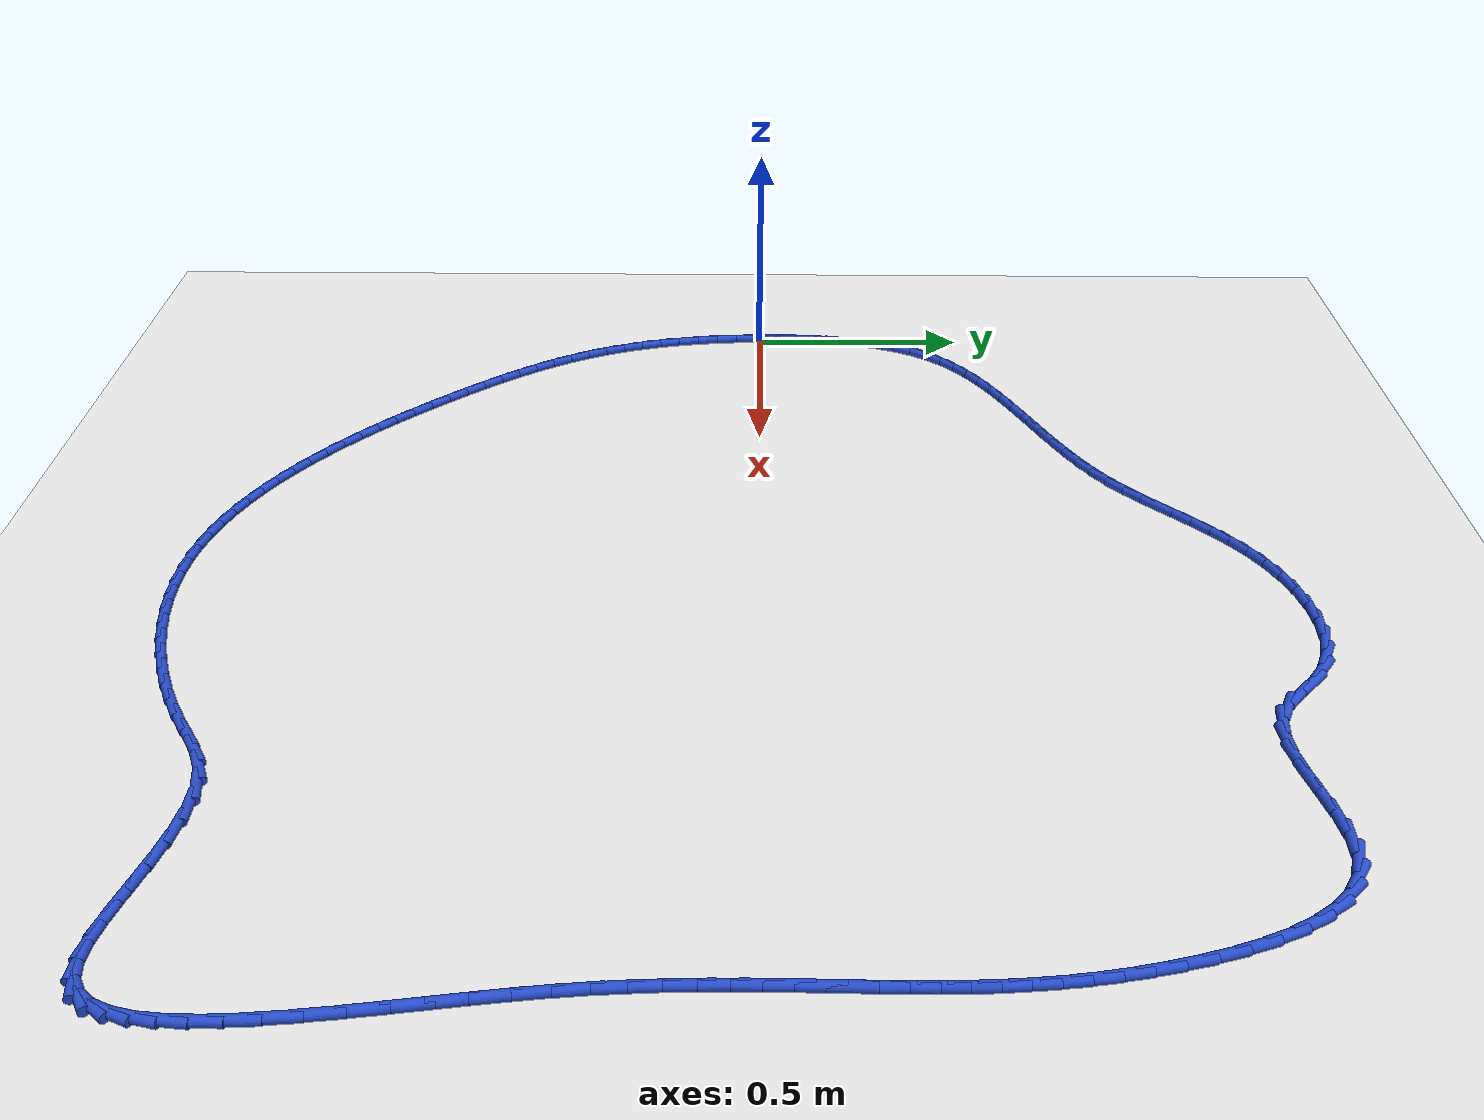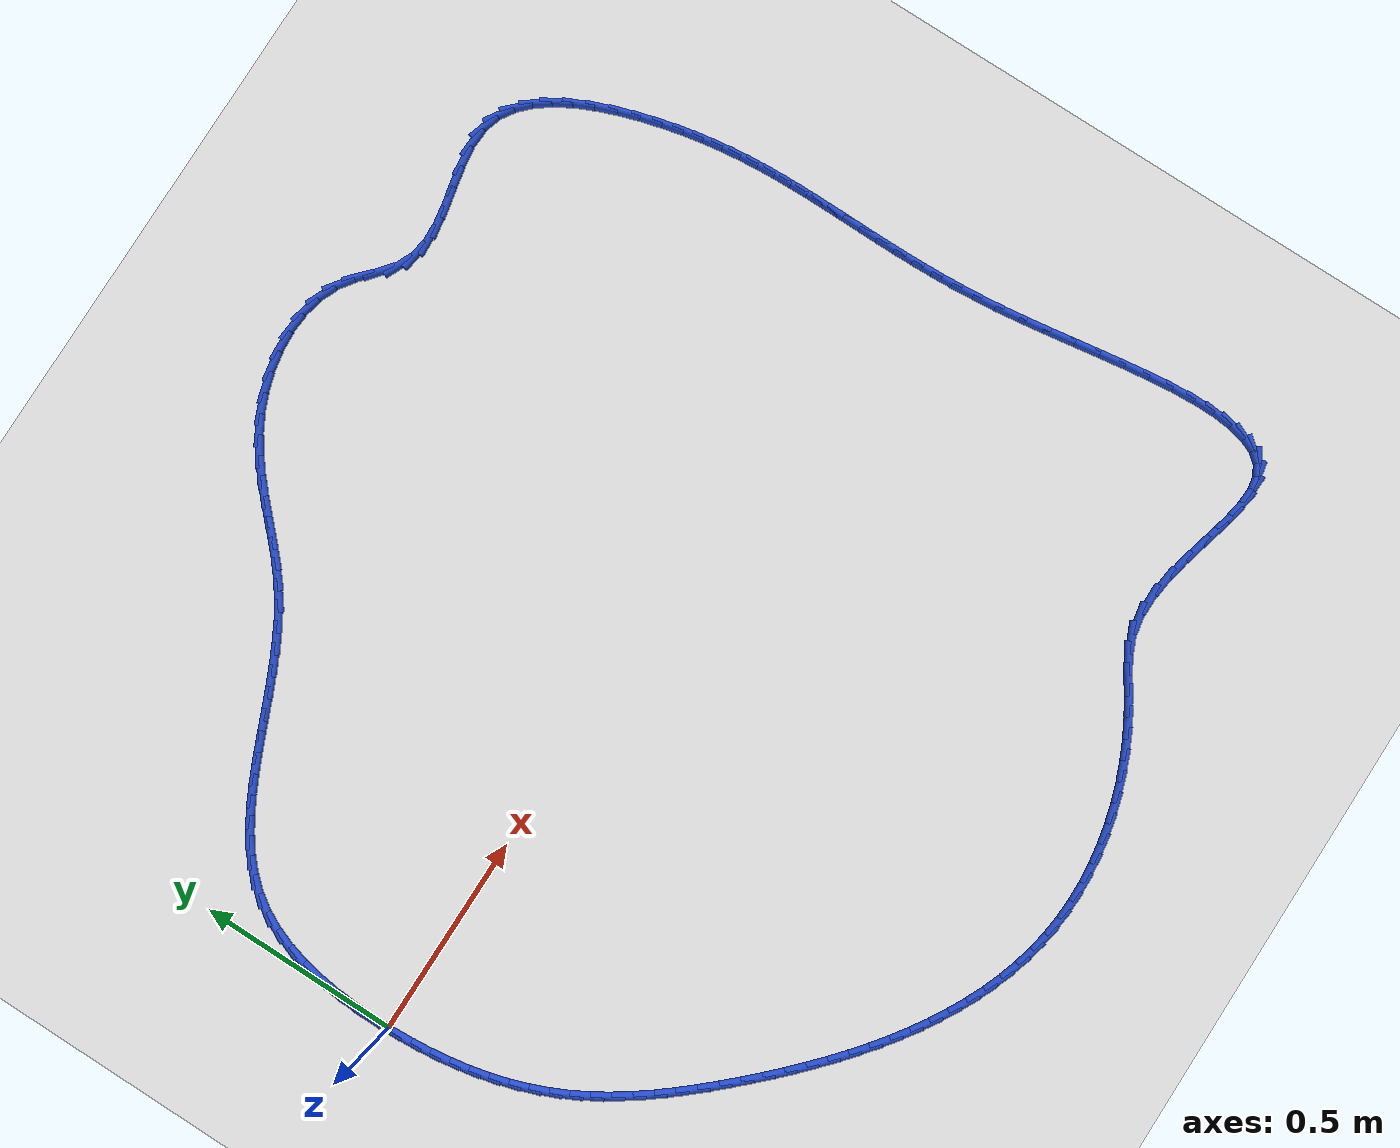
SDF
<sdf version="1.6">
 <world name="default">
  <light name="sun" type="directional">
   <pose>0 0 10 0 -0 0</pose>
   <diffuse>0.8 0.8 0.8 1</diffuse>
   <specular>0.2 0.2 0.2 1</specular>
   <attenuation>
    <range>1000</range>
    <constant>0.9</constant>
    <linear>0.01</linear>
    <quadratic>0.001</quadratic>
   </attenuation>
   <direction>-0.5 0.1 -0.9</direction>
  </light>
  <model name="ground_plane">
   <static>1</static>
   <link name="link">
    <collision name="collision">
     <geometry><plane><normal>0 0 1</normal><size>100 100</size></plane></geometry>
     <surface><friction><ode><mu>100</mu><mu2>50</mu2></ode></friction></surface>
    </collision>
    <visual name="visual">
     <cast_shadows>0</cast_shadows>
     <geometry><plane><normal>0 0 1</normal><size>100 100</size></plane></geometry>
     <material>
      <script><uri>file://media/materials/scripts/gazebo.material</uri><name>Gazebo/WhiteGlow</name></script>
     </material>
    </visual>
   </link>
  </model>
  <gravity>0 0 -9.8</gravity>
  <magnetic_field>6e-06 2.3e-05 -4.2e-05</magnetic_field>
  <atmosphere type="adiabatic"/>
  <physics name="default_physics" default="0" type="ode">
   <max_step_size>0.001</max_step_size>
   <real_time_factor>1</real_time_factor>
   <real_time_update_rate>1000</real_time_update_rate>
  </physics>
  <scene><ambient>0.4 0.4 0.4 1</ambient><background>0.7 0.7 0.7 1</background><shadows>1</shadows></scene>
  <spherical_coordinates>
   <surface_model>EARTH_WGS84</surface_model>
   <latitude_deg>0</latitude_deg>
   <longitude_deg>0</longitude_deg>
   <elevation>0</elevation>
   <heading_deg>0</heading_deg>
  </spherical_coordinates>
  <model name="line">
   <link name="link_0">
    <pose>-1.3877787807814457e-17 1.3877787807814457e-17 0.01 0 1.57 -1.560731636557664</pose>
    <collision name="collision">
     <geometry><cylinder><radius>0.01</radius><length>0.08</length></cylinder></geometry>
    </collision>
    <visual name="visual">
     <material>
      <script><name>Gazebo/Blue</name><uri>file://media/materials/scripts/gazebo.material</uri></script>
     </material>
     <geometry><cylinder><radius>0.01</radius><length>0.08</length></cylinder></geometry>
    </visual>
   </link>
   <link name="link_1">
    <pose>-0.0005223845337130366 0.051900941056998405 0.01 0 1.57 1.5402072996749345</pose>
    <collision name="collision">
     <geometry><cylinder><radius>0.01</radius><length>0.08</length></cylinder></geometry>
    </collision>
    <visual name="visual">
     <material>
      <script><name>Gazebo/Blue</name><uri>file://media/materials/scripts/gazebo.material</uri></script>
     </material>
     <geometry><cylinder><radius>0.01</radius><length>0.08</length></cylinder></geometry>
    </visual>
   </link>
   <link name="link_2">
    <pose>0.0010700641967369999 0.10394417912810257 0.01 0 1.57 1.4924301519347458</pose>
    <collision name="collision">
     <geometry><cylinder><radius>0.01</radius><length>0.08</length></cylinder></geometry>
    </collision>
    <visual name="visual">
     <material>
      <script><name>Gazebo/Blue</name><uri>file://media/materials/scripts/gazebo.material</uri></script>
     </material>
     <geometry><cylinder><radius>0.01</radius><length>0.08</length></cylinder></geometry>
    </visual>
   </link>
   <link name="link_3">
    <pose>0.005124552543725727 0.15557595863801021 0.01 0 1.57 1.4361473055702652</pose>
    <collision name="collision">
     <geometry><cylinder><radius>0.01</radius><length>0.08</length></cylinder></geometry>
    </collision>
    <visual name="visual">
     <material>
      <script><name>Gazebo/Blue</name><uri>file://media/materials/scripts/gazebo.material</uri></script>
     </material>
     <geometry><cylinder><radius>0.01</radius><length>0.08</length></cylinder></geometry>
    </visual>
   </link>
   <link name="link_4">
    <pose>0.011988286859628777 0.2062425240114192 0.01 0 1.57 1.3696732882570835</pose>
    <collision name="collision">
     <geometry><cylinder><radius>0.01</radius><length>0.08</length></cylinder></geometry>
    </collision>
    <visual name="visual">
     <material>
      <script><name>Gazebo/Blue</name><uri>file://media/materials/scripts/gazebo.material</uri></script>
     </material>
     <geometry><cylinder><radius>0.01</radius><length>0.08</length></cylinder></geometry>
    </visual>
   </link>
   <link name="link_5">
    <pose>0.02200847349682178 0.25539011967302727 0.01 0 1.57 1.291046255590493</pose>
    <collision name="collision">
     <geometry><cylinder><radius>0.01</radius><length>0.08</length></cylinder></geometry>
    </collision>
    <visual name="visual">
     <material>
      <script><name>Gazebo/Blue</name><uri>file://media/materials/scripts/gazebo.material</uri></script>
     </material>
     <geometry><cylinder><radius>0.01</radius><length>0.08</length></cylinder></geometry>
    </visual>
   </link>
   <link name="link_6">
    <pose>0.03553231880768039 0.30246499004753236 0.01 0 1.57 1.19816253137743</pose>
    <collision name="collision">
     <geometry><cylinder><radius>0.01</radius><length>0.08</length></cylinder></geometry>
    </collision>
    <visual name="visual">
     <material>
      <script><name>Gazebo/Blue</name><uri>file://media/materials/scripts/gazebo.material</uri></script>
     </material>
     <geometry><cylinder><radius>0.01</radius><length>0.08</length></cylinder></geometry>
    </visual>
   </link>
   <link name="link_7">
    <pose>0.052907029144580196 0.3469133795596321 0.01 0 1.57 1.0891175648220033</pose>
    <collision name="collision">
     <geometry><cylinder><radius>0.01</radius><length>0.08</length></cylinder></geometry>
    </collision>
    <visual name="visual">
     <material>
      <script><name>Gazebo/Blue</name><uri>file://media/materials/scripts/gazebo.material</uri></script>
     </material>
     <geometry><cylinder><radius>0.01</radius><length>0.08</length></cylinder></geometry>
    </visual>
   </link>
   <link name="link_8">
    <pose>0.07447981085989688 0.38818153263402444 0.01 0 1.57 0.9635173999993287</pose>
    <collision name="collision">
     <geometry><cylinder><radius>0.01</radius><length>0.08</length></cylinder></geometry>
    </collision>
    <visual name="visual">
     <material>
      <script><name>Gazebo/Blue</name><uri>file://media/materials/scripts/gazebo.material</uri></script>
     </material>
     <geometry><cylinder><radius>0.01</radius><length>0.08</length></cylinder></geometry>
    </visual>
   </link>
   <link name="link_9">
    <pose>0.10057786827884474 0.4257393814733775 0.01 0 1.57 0.8364470968662366</pose>
    <collision name="collision">
     <geometry><cylinder><radius>0.01</radius><length>0.08</length></cylinder></geometry>
    </collision>
    <visual name="visual">
     <material>
      <script><name>Gazebo/Blue</name><uri>file://media/materials/scripts/gazebo.material</uri></script>
     </material>
     <geometry><cylinder><radius>0.01</radius><length>0.08</length></cylinder></geometry>
    </visual>
   </link>
   <link name="link_10">
    <pose>0.13110689368760722 0.45955604186369553 0.01 0 1.57 0.7247675098538062</pose>
    <collision name="collision">
     <geometry><cylinder><radius>0.01</radius><length>0.08</length></cylinder></geometry>
    </collision>
    <visual name="visual">
     <material>
      <script><name>Gazebo/Blue</name><uri>file://media/materials/scripts/gazebo.material</uri></script>
     </material>
     <geometry><cylinder><radius>0.01</radius><length>0.08</length></cylinder></geometry>
    </visual>
   </link>
   <link name="link_11">
    <pose>0.16557142511147901 0.49007570409154055 0.01 0 1.57 0.6310425393310027</pose>
    <collision name="collision">
     <geometry><cylinder><radius>0.01</radius><length>0.08</length></cylinder></geometry>
    </collision>
    <visual name="visual">
     <material>
      <script><name>Gazebo/Blue</name><uri>file://media/materials/scripts/gazebo.material</uri></script>
     </material>
     <geometry><cylinder><radius>0.01</radius><length>0.08</length></cylinder></geometry>
    </visual>
   </link>
   <link name="link_12">
    <pose>0.2034600732321568 0.5177614207005721 0.01 0 1.57 0.5553138125785149</pose>
    <collision name="collision">
     <geometry><cylinder><radius>0.01</radius><length>0.08</length></cylinder></geometry>
    </collision>
    <visual name="visual">
     <material>
      <script><name>Gazebo/Blue</name><uri>file://media/materials/scripts/gazebo.material</uri></script>
     </material>
     <geometry><cylinder><radius>0.01</radius><length>0.08</length></cylinder></geometry>
    </visual>
   </link>
   <link name="link_13">
    <pose>0.24426144873133718 0.5430762442344499 0.01 0 1.57 0.4965214114239881</pose>
    <collision name="collision">
     <geometry><cylinder><radius>0.01</radius><length>0.08</length></cylinder></geometry>
    </collision>
    <visual name="visual">
     <material>
      <script><name>Gazebo/Blue</name><uri>file://media/materials/scripts/gazebo.material</uri></script>
     </material>
     <geometry><cylinder><radius>0.01</radius><length>0.08</length></cylinder></geometry>
    </visual>
   </link>
   <link name="link_14">
    <pose>0.28746416229071675 0.5664832272368336 0.01 0 1.57 0.45323070438526</pose>
    <collision name="collision">
     <geometry><cylinder><radius>0.01</radius><length>0.08</length></cylinder></geometry>
    </collision>
    <visual name="visual">
     <material>
      <script><name>Gazebo/Blue</name><uri>file://media/materials/scripts/gazebo.material</uri></script>
     </material>
     <geometry><cylinder><radius>0.01</radius><length>0.08</length></cylinder></geometry>
    </visual>
   </link>
   <link name="link_15">
    <pose>0.3325568245919923 0.5884454222513835 0.01 0 1.57 0.42407744229642985</pose>
    <collision name="collision">
     <geometry><cylinder><radius>0.01</radius><length>0.08</length></cylinder></geometry>
    </collision>
    <visual name="visual">
     <material>
      <script><name>Gazebo/Blue</name><uri>file://media/materials/scripts/gazebo.material</uri></script>
     </material>
     <geometry><cylinder><radius>0.01</radius><length>0.08</length></cylinder></geometry>
    </visual>
   </link>
   <link name="link_16">
    <pose>0.3790280463168604 0.6094258818217587 0.01 0 1.57 0.4079910725440669</pose>
    <collision name="collision">
     <geometry><cylinder><radius>0.01</radius><length>0.08</length></cylinder></geometry>
    </collision>
    <visual name="visual">
     <material>
      <script><name>Gazebo/Blue</name><uri>file://media/materials/scripts/gazebo.material</uri></script>
     </material>
     <geometry><cylinder><radius>0.01</radius><length>0.08</length></cylinder></geometry>
    </visual>
   </link>
   <link name="link_17">
    <pose>0.4263664381470178 0.6298876584916195 0.01 0 1.57 0.4042855924578332</pose>
    <collision name="collision">
     <geometry><cylinder><radius>0.01</radius><length>0.08</length></cylinder></geometry>
    </collision>
    <visual name="visual">
     <material>
      <script><name>Gazebo/Blue</name><uri>file://media/materials/scripts/gazebo.material</uri></script>
     </material>
     <geometry><cylinder><radius>0.01</radius><length>0.08</length></cylinder></geometry>
    </visual>
   </link>
   <link name="link_18">
    <pose>0.474060610764161 0.6502938048046254 0.01 0 1.57 0.41268313730122974</pose>
    <collision name="collision">
     <geometry><cylinder><radius>0.01</radius><length>0.08</length></cylinder></geometry>
    </collision>
    <visual name="visual">
     <material>
      <script><name>Gazebo/Blue</name><uri>file://media/materials/scripts/gazebo.material</uri></script>
     </material>
     <geometry><cylinder><radius>0.01</radius><length>0.08</length></cylinder></geometry>
    </visual>
   </link>
   <link name="link_19">
    <pose>0.521599174849987 0.6711073733044365 0.01 0 1.57 0.4333046288963181</pose>
    <collision name="collision">
     <geometry><cylinder><radius>0.01</radius><length>0.08</length></cylinder></geometry>
    </collision>
    <visual name="visual">
     <material>
      <script><name>Gazebo/Blue</name><uri>file://media/materials/scripts/gazebo.material</uri></script>
     </material>
     <geometry><cylinder><radius>0.01</radius><length>0.08</length></cylinder></geometry>
    </visual>
   </link>
   <link name="link_20">
    <pose>0.568470741086192 0.6927914165347122 0.01 0 1.57 0.46663667525193436</pose>
    <collision name="collision">
     <geometry><cylinder><radius>0.01</radius><length>0.08</length></cylinder></geometry>
    </collision>
    <visual name="visual">
     <material>
      <script><name>Gazebo/Blue</name><uri>file://media/materials/scripts/gazebo.material</uri></script>
     </material>
     <geometry><cylinder><radius>0.01</radius><length>0.08</length></cylinder></geometry>
    </visual>
   </link>
   <link name="link_21">
    <pose>0.6141639201544731 0.7158089870391124 0.01 0 1.57 0.5134632160605139</pose>
    <collision name="collision">
     <geometry><cylinder><radius>0.01</radius><length>0.08</length></cylinder></geometry>
    </collision>
    <visual name="visual">
     <material>
      <script><name>Gazebo/Blue</name><uri>file://media/materials/scripts/gazebo.material</uri></script>
     </material>
     <geometry><cylinder><radius>0.01</radius><length>0.08</length></cylinder></geometry>
    </visual>
   </link>
   <link name="link_22">
    <pose>0.6581673227365265 0.7406231373612968 0.01 0 1.57 0.5747309308227962</pose>
    <collision name="collision">
     <geometry><cylinder><radius>0.01</radius><length>0.08</length></cylinder></geometry>
    </collision>
    <visual name="visual">
     <material>
      <script><name>Gazebo/Blue</name><uri>file://media/materials/scripts/gazebo.material</uri></script>
     </material>
     <geometry><cylinder><radius>0.01</radius><length>0.08</length></cylinder></geometry>
    </visual>
   </link>
   <link name="link_23">
    <pose>0.6999695595140495 0.7676969200449257 0.01 0 1.57 0.6483174393849604</pose>
    <collision name="collision">
     <geometry><cylinder><radius>0.01</radius><length>0.08</length></cylinder></geometry>
    </collision>
    <visual name="visual">
     <material>
      <script><name>Gazebo/Blue</name><uri>file://media/materials/scripts/gazebo.material</uri></script>
     </material>
     <geometry><cylinder><radius>0.01</radius><length>0.08</length></cylinder></geometry>
    </visual>
   </link>
   <link name="link_24">
    <pose>0.7391666643884603 0.797390798857896 0.01 0 1.57 0.7107254150960269</pose>
    <collision name="collision">
     <geometry><cylinder><radius>0.01</radius><length>0.08</length></cylinder></geometry>
    </collision>
    <visual name="visual">
     <material>
      <script><name>Gazebo/Blue</name><uri>file://media/materials/scripts/gazebo.material</uri></script>
     </material>
     <geometry><cylinder><radius>0.01</radius><length>0.08</length></cylinder></geometry>
    </visual>
   </link>
   <link name="link_25">
    <pose>0.776194051309364 0.8292636327403522 0.01 0 1.57 0.7498045570435847</pose>
    <collision name="collision">
     <geometry><cylinder><radius>0.01</radius><length>0.08</length></cylinder></geometry>
    </collision>
    <visual name="visual">
     <material>
      <script><name>Gazebo/Blue</name><uri>file://media/materials/scripts/gazebo.material</uri></script>
     </material>
     <geometry><cylinder><radius>0.01</radius><length>0.08</length></cylinder></geometry>
    </visual>
   </link>
   <link name="link_26">
    <pose>0.8118819002451658 0.8624972805510219 0.01 0 1.57 0.765001297310169</pose>
    <collision name="collision">
     <geometry><cylinder><radius>0.01</radius><length>0.08</length></cylinder></geometry>
    </collision>
    <visual name="visual">
     <material>
      <script><name>Gazebo/Blue</name><uri>file://media/materials/scripts/gazebo.material</uri></script>
     </material>
     <geometry><cylinder><radius>0.01</radius><length>0.08</length></cylinder></geometry>
    </visual>
   </link>
   <link name="link_27">
    <pose>0.847062687291403 0.8962714083557525 0.01 0 1.57 0.7562482554368029</pose>
    <collision name="collision">
     <geometry><cylinder><radius>0.01</radius><length>0.08</length></cylinder></geometry>
    </collision>
    <visual name="visual">
     <material>
      <script><name>Gazebo/Blue</name><uri>file://media/materials/scripts/gazebo.material</uri></script>
     </material>
     <geometry><cylinder><radius>0.01</radius><length>0.08</length></cylinder></geometry>
    </visual>
   </link>
   <link name="link_28">
    <pose>0.8825688885436133 0.9297656822203908 0.01 0 1.57 0.7236447770030061</pose>
    <collision name="collision">
     <geometry><cylinder><radius>0.01</radius><length>0.08</length></cylinder></geometry>
    </collision>
    <visual name="visual">
     <material>
      <script><name>Gazebo/Blue</name><uri>file://media/materials/scripts/gazebo.material</uri></script>
     </material>
     <geometry><cylinder><radius>0.01</radius><length>0.08</length></cylinder></geometry>
    </visual>
   </link>
   <link name="link_29">
    <pose>0.919232980097334 0.9621597682107836 0.01 0 1.57 0.6676019463689604</pose>
    <collision name="collision">
     <geometry><cylinder><radius>0.01</radius><length>0.08</length></cylinder></geometry>
    </collision>
    <visual name="visual">
     <material>
      <script><name>Gazebo/Blue</name><uri>file://media/materials/scripts/gazebo.material</uri></script>
     </material>
     <geometry><cylinder><radius>0.01</radius><length>0.08</length></cylinder></geometry>
    </visual>
   </link>
   <link name="link_30">
    <pose>0.9578874380481026 0.9926333323927783 0.01 0 1.57 0.5893562884456904</pose>
    <collision name="collision">
     <geometry><cylinder><radius>0.01</radius><length>0.08</length></cylinder></geometry>
    </collision>
    <visual name="visual">
     <material>
      <script><name>Gazebo/Blue</name><uri>file://media/materials/scripts/gazebo.material</uri></script>
     </material>
     <geometry><cylinder><radius>0.01</radius><length>0.08</length></cylinder></geometry>
    </visual>
   </link>
   <link name="link_31">
    <pose>0.9993647384914577 1.0203660408322224 0.01 0 1.57 0.4920395509079483</pose>
    <collision name="collision">
     <geometry><cylinder><radius>0.01</radius><length>0.08</length></cylinder></geometry>
    </collision>
    <visual name="visual">
     <material>
      <script><name>Gazebo/Blue</name><uri>file://media/materials/scripts/gazebo.material</uri></script>
     </material>
     <geometry><cylinder><radius>0.01</radius><length>0.08</length></cylinder></geometry>
    </visual>
   </link>
   <link name="link_32">
    <pose>1.0444641228149922 1.0445397984660865 0.01 0 1.57 0.38790882425388795</pose>
    <collision name="collision">
     <geometry><cylinder><radius>0.01</radius><length>0.08</length></cylinder></geometry>
    </collision>
    <visual name="visual">
     <material>
      <script><name>Gazebo/Blue</name><uri>file://media/materials/scripts/gazebo.material</uri></script>
     </material>
     <geometry><cylinder><radius>0.01</radius><length>0.08</length></cylinder></geometry>
    </visual>
   </link>
   <link name="link_33">
    <pose>1.0930644766308868 1.064398510414211 0.01 0 1.57 0.2836419325629583</pose>
    <collision name="collision">
     <geometry><cylinder><radius>0.01</radius><length>0.08</length></cylinder></geometry>
    </collision>
    <visual name="visual">
     <material>
      <script><name>Gazebo/Blue</name><uri>file://media/materials/scripts/gazebo.material</uri></script>
     </material>
     <geometry><cylinder><radius>0.01</radius><length>0.08</length></cylinder></geometry>
    </visual>
   </link>
   <link name="link_34">
    <pose>1.1440283196683876 1.0792545497435986 0.01 0 1.57 0.17408744583447866</pose>
    <collision name="collision">
     <geometry><cylinder><radius>0.01</radius><length>0.08</length></cylinder></geometry>
    </collision>
    <visual name="visual">
     <material>
      <script><name>Gazebo/Blue</name><uri>file://media/materials/scripts/gazebo.material</uri></script>
     </material>
     <geometry><cylinder><radius>0.01</radius><length>0.08</length></cylinder></geometry>
    </visual>
   </link>
   <link name="link_35">
    <pose>1.1961656756387722 1.0884238259392338 0.01 0 1.57 0.053639491239369064</pose>
    <collision name="collision">
     <geometry><cylinder><radius>0.01</radius><length>0.08</length></cylinder></geometry>
    </collision>
    <visual name="visual">
     <material>
      <script><name>Gazebo/Blue</name><uri>file://media/materials/scripts/gazebo.material</uri></script>
     </material>
     <geometry><cylinder><radius>0.01</radius><length>0.08</length></cylinder></geometry>
    </visual>
   </link>
   <link name="link_36">
    <pose>1.2482865682533189 1.091222248486101 0.01 0 1.57 -0.08340748425018744</pose>
    <collision name="collision">
     <geometry><cylinder><radius>0.01</radius><length>0.08</length></cylinder></geometry>
    </collision>
    <visual name="visual">
     <material>
      <script><name>Gazebo/Blue</name><uri>file://media/materials/scripts/gazebo.material</uri></script>
     </material>
     <geometry><cylinder><radius>0.01</radius><length>0.08</length></cylinder></geometry>
    </visual>
   </link>
   <link name="link_37">
    <pose>1.2992010212233052 1.0869657268691848 0.01 0 1.57 -0.24237849514918086</pose>
    <collision name="collision">
     <geometry><cylinder><radius>0.01</radius><length>0.08</length></cylinder></geometry>
    </collision>
    <visual name="visual">
     <material>
      <script><name>Gazebo/Blue</name><uri>file://media/materials/scripts/gazebo.material</uri></script>
     </material>
     <geometry><cylinder><radius>0.01</radius><length>0.08</length></cylinder></geometry>
    </visual>
   </link>
   <link name="link_38">
    <pose>1.347719058260009 1.0749701705734702 0.01 0 1.57 -0.42653907451353473</pose>
    <collision name="collision">
     <geometry><cylinder><radius>0.01</radius><length>0.08</length></cylinder></geometry>
    </collision>
    <visual name="visual">
     <material>
      <script><name>Gazebo/Blue</name><uri>file://media/materials/scripts/gazebo.material</uri></script>
     </material>
     <geometry><cylinder><radius>0.01</radius><length>0.08</length></cylinder></geometry>
    </visual>
   </link>
   <link name="link_39">
    <pose>1.3926507030747077 1.0545514890839418 0.01 0 1.57 -0.6294814415179085</pose>
    <collision name="collision">
     <geometry><cylinder><radius>0.01</radius><length>0.08</length></cylinder></geometry>
    </collision>
    <visual name="visual">
     <material>
      <script><name>Gazebo/Blue</name><uri>file://media/materials/scripts/gazebo.material</uri></script>
     </material>
     <geometry><cylinder><radius>0.01</radius><length>0.08</length></cylinder></geometry>
    </visual>
   </link>
   <link name="link_40">
    <pose>1.4329145899051385 1.0252264627812258 0.01 0 1.57 -0.7468671732004298</pose>
    <collision name="collision">
     <geometry><cylinder><radius>0.01</radius><length>0.08</length></cylinder></geometry>
    </collision>
    <visual name="visual">
     <material>
      <script><name>Gazebo/Blue</name><uri>file://media/materials/scripts/gazebo.material</uri></script>
     </material>
     <geometry><cylinder><radius>0.01</radius><length>0.08</length></cylinder></geometry>
    </visual>
   </link>
   <link name="link_41">
    <pose>1.4698659660813262 0.9910182920969072 0.01 0 1.57 -0.6861508142728906</pose>
    <collision name="collision">
     <geometry><cylinder><radius>0.01</radius><length>0.08</length></cylinder></geometry>
    </collision>
    <visual name="visual">
     <material>
      <script><name>Gazebo/Blue</name><uri>file://media/materials/scripts/gazebo.material</uri></script>
     </material>
     <geometry><cylinder><radius>0.01</radius><length>0.08</length></cylinder></geometry>
    </visual>
   </link>
   <link name="link_42">
    <pose>1.5072630456528717 0.9603943698709438 0.01 0 1.57 -0.4293373047036167</pose>
    <collision name="collision">
     <geometry><cylinder><radius>0.01</radius><length>0.08</length></cylinder></geometry>
    </collision>
    <visual name="visual">
     <material>
      <script><name>Gazebo/Blue</name><uri>file://media/materials/scripts/gazebo.material</uri></script>
     </material>
     <geometry><cylinder><radius>0.01</radius><length>0.08</length></cylinder></geometry>
    </visual>
   </link>
   <link name="link_43">
    <pose>1.548712986838111 0.9414177915825171 0.01 0 1.57 -0.13399790288748445</pose>
    <collision name="collision">
     <geometry><cylinder><radius>0.01</radius><length>0.08</length></cylinder></geometry>
    </collision>
    <visual name="visual">
     <material>
      <script><name>Gazebo/Blue</name><uri>file://media/materials/scripts/gazebo.material</uri></script>
     </material>
     <geometry><cylinder><radius>0.01</radius><length>0.08</length></cylinder></geometry>
    </visual>
   </link>
   <link name="link_44">
    <pose>1.5948553656058173 0.9351975358138063 0.01 0 1.57 0.06304998692201866</pose>
    <collision name="collision">
     <geometry><cylinder><radius>0.01</radius><length>0.08</length></cylinder></geometry>
    </collision>
    <visual name="visual">
     <material>
      <script><name>Gazebo/Blue</name><uri>file://media/materials/scripts/gazebo.material</uri></script>
     </material>
     <geometry><cylinder><radius>0.01</radius><length>0.08</length></cylinder></geometry>
    </visual>
   </link>
   <link name="link_45">
    <pose>1.644402196647742 0.938325608972584 0.01 0 1.57 0.17242606579460498</pose>
    <collision name="collision">
     <geometry><cylinder><radius>0.01</radius><length>0.08</length></cylinder></geometry>
    </collision>
    <visual name="visual">
     <material>
      <script><name>Gazebo/Blue</name><uri>file://media/materials/scripts/gazebo.material</uri></script>
     </material>
     <geometry><cylinder><radius>0.01</radius><length>0.08</length></cylinder></geometry>
    </visual>
   </link>
   <link name="link_46">
    <pose>1.696032779856192 0.9473173548771904 0.01 0 1.57 0.2137114982523742</pose>
    <collision name="collision">
     <geometry><cylinder><radius>0.01</radius><length>0.08</length></cylinder></geometry>
    </collision>
    <visual name="visual">
     <material>
      <script><name>Gazebo/Blue</name><uri>file://media/materials/scripts/gazebo.material</uri></script>
     </material>
     <geometry><cylinder><radius>0.01</radius><length>0.08</length></cylinder></geometry>
    </visual>
   </link>
   <link name="link_47">
    <pose>1.7484264151234732 0.9586881173459646 0.01 0 1.57 0.19550139874099487</pose>
    <collision name="collision">
     <geometry><cylinder><radius>0.01</radius><length>0.08</length></cylinder></geometry>
    </collision>
    <visual name="visual">
     <material>
      <script><name>Gazebo/Blue</name><uri>file://media/materials/scripts/gazebo.material</uri></script>
     </material>
     <geometry><cylinder><radius>0.01</radius><length>0.08</length></cylinder></geometry>
    </visual>
   </link>
   <link name="link_48">
    <pose>1.8002624023418914 0.9689532401972458 0.01 0 1.57 0.11310795236327678</pose>
    <collision name="collision">
     <geometry><cylinder><radius>0.01</radius><length>0.08</length></cylinder></geometry>
    </collision>
    <visual name="visual">
     <material>
      <script><name>Gazebo/Blue</name><uri>file://media/materials/scripts/gazebo.material</uri></script>
     </material>
     <geometry><cylinder><radius>0.01</radius><length>0.08</length></cylinder></geometry>
    </visual>
   </link>
   <link name="link_49">
    <pose>1.850220041403754 0.9746280672493743 0.01 0 1.57 -0.0512851280952237</pose>
    <collision name="collision">
     <geometry><cylinder><radius>0.01</radius><length>0.08</length></cylinder></geometry>
    </collision>
    <visual name="visual">
     <material>
      <script><name>Gazebo/Blue</name><uri>file://media/materials/scripts/gazebo.material</uri></script>
     </material>
     <geometry><cylinder><radius>0.01</radius><length>0.08</length></cylinder></geometry>
    </visual>
   </link>
   <link name="link_50">
    <pose>1.8969786322013666 0.9722279423206889 0.01 0 1.57 -0.30920133902874697</pose>
    <collision name="collision">
     <geometry><cylinder><radius>0.01</radius><length>0.08</length></cylinder></geometry>
    </collision>
    <visual name="visual">
     <material>
      <script><name>Gazebo/Blue</name><uri>file://media/materials/scripts/gazebo.material</uri></script>
     </material>
     <geometry><cylinder><radius>0.01</radius><length>0.08</length></cylinder></geometry>
    </visual>
   </link>
   <link name="link_51">
    <pose>1.9393470703888034 0.9586934668144883 0.01 0 1.57 -0.5742188186803635</pose>
    <collision name="collision">
     <geometry><cylinder><radius>0.01</radius><length>0.08</length></cylinder></geometry>
    </collision>
    <visual name="visual">
     <material>
      <script><name>Gazebo/Blue</name><uri>file://media/materials/scripts/gazebo.material</uri></script>
     </material>
     <geometry><cylinder><radius>0.01</radius><length>0.08</length></cylinder></geometry>
    </visual>
   </link>
   <link name="link_52">
    <pose>1.9771344782977258 0.9342474017935839 0.01 0 1.57 -0.787284432630587</pose>
    <collision name="collision">
     <geometry><cylinder><radius>0.01</radius><length>0.08</length></cylinder></geometry>
    </collision>
    <visual name="visual">
     <material>
      <script><name>Gazebo/Blue</name><uri>file://media/materials/scripts/gazebo.material</uri></script>
     </material>
     <geometry><cylinder><radius>0.01</radius><length>0.08</length></cylinder></geometry>
    </visual>
   </link>
   <link name="link_53">
    <pose>2.0106154426083465 0.9006398904052688 0.01 0 1.57 -0.9479905221870754</pose>
    <collision name="collision">
     <geometry><cylinder><radius>0.01</radius><length>0.08</length></cylinder></geometry>
    </collision>
    <visual name="visual">
     <material>
      <script><name>Gazebo/Blue</name><uri>file://media/materials/scripts/gazebo.material</uri></script>
     </material>
     <geometry><cylinder><radius>0.01</radius><length>0.08</length></cylinder></geometry>
    </visual>
   </link>
   <link name="link_54">
    <pose>2.0400671394477903 0.8596295728489362 0.01 0 1.57 -1.067301034450368</pose>
    <collision name="collision">
     <geometry><cylinder><radius>0.01</radius><length>0.08</length></cylinder></geometry>
    </collision>
    <visual name="visual">
     <material>
      <script><name>Gazebo/Blue</name><uri>file://media/materials/scripts/gazebo.material</uri></script>
     </material>
     <geometry><cylinder><radius>0.01</radius><length>0.08</length></cylinder></geometry>
    </visual>
   </link>
   <link name="link_55">
    <pose>2.0657667449431827 0.8129750893239805 0.01 0 1.57 -1.1565035445850742</pose>
    <collision name="collision">
     <geometry><cylinder><radius>0.01</radius><length>0.08</length></cylinder></geometry>
    </collision>
    <visual name="visual">
     <material>
      <script><name>Gazebo/Blue</name><uri>file://media/materials/scripts/gazebo.material</uri></script>
     </material>
     <geometry><cylinder><radius>0.01</radius><length>0.08</length></cylinder></geometry>
    </visual>
   </link>
   <link name="link_56">
    <pose>2.0879914352216478 0.762435080029795 0.01 0 1.57 -1.2241172107202294</pose>
    <collision name="collision">
     <geometry><cylinder><radius>0.01</radius><length>0.08</length></cylinder></geometry>
    </collision>
    <visual name="visual">
     <material>
      <script><name>Gazebo/Blue</name><uri>file://media/materials/scripts/gazebo.material</uri></script>
     </material>
     <geometry><cylinder><radius>0.01</radius><length>0.08</length></cylinder></geometry>
    </visual>
   </link>
   <link name="link_57">
    <pose>2.10701838641031 0.7097681851657731 0.01 0 1.57 -1.275955129877135</pose>
    <collision name="collision">
     <geometry><cylinder><radius>0.01</radius><length>0.08</length></cylinder></geometry>
    </collision>
    <visual name="visual">
     <material>
      <script><name>Gazebo/Blue</name><uri>file://media/materials/scripts/gazebo.material</uri></script>
     </material>
     <geometry><cylinder><radius>0.01</radius><length>0.08</length></cylinder></geometry>
    </visual>
   </link>
   <link name="link_58">
    <pose>2.1231247746362953 0.6567330449313074 0.01 0 1.57 -1.3165396528618019</pose>
    <collision name="collision">
     <geometry><cylinder><radius>0.01</radius><length>0.08</length></cylinder></geometry>
    </collision>
    <visual name="visual">
     <material>
      <script><name>Gazebo/Blue</name><uri>file://media/materials/scripts/gazebo.material</uri></script>
     </material>
     <geometry><cylinder><radius>0.01</radius><length>0.08</length></cylinder></geometry>
    </visual>
   </link>
   <link name="link_59">
    <pose>2.1365840468953263 0.6049429269997217 0.01 0 1.57 -1.353860161787056</pose>
    <collision name="collision">
     <geometry><cylinder><radius>0.01</radius><length>0.08</length></cylinder></geometry>
    </collision>
    <visual name="visual">
     <material>
      <script><name>Gazebo/Blue</name><uri>file://media/materials/scripts/gazebo.material</uri></script>
     </material>
     <geometry><cylinder><radius>0.01</radius><length>0.08</length></cylinder></geometry>
    </visual>
   </link>
   <link name="link_60">
    <pose>2.14763829028107 0.5547885976920731 0.01 0 1.57 -1.3906673325039391</pose>
    <collision name="collision">
     <geometry><cylinder><radius>0.01</radius><length>0.08</length></cylinder></geometry>
    </collision>
    <visual name="visual">
     <material>
      <script><name>Gazebo/Blue</name><uri>file://media/materials/scripts/gazebo.material</uri></script>
     </material>
     <geometry><cylinder><radius>0.01</radius><length>0.08</length></cylinder></geometry>
    </visual>
   </link>
   <link name="link_61">
    <pose>2.1565138984983276 0.50604904880699 0.01 0 1.57 -1.4262139118599615</pose>
    <collision name="collision">
     <geometry><cylinder><radius>0.01</radius><length>0.08</length></cylinder></geometry>
    </collision>
    <visual name="visual">
     <material>
      <script><name>Gazebo/Blue</name><uri>file://media/materials/scripts/gazebo.material</uri></script>
     </material>
     <geometry><cylinder><radius>0.01</radius><length>0.08</length></cylinder></geometry>
    </visual>
   </link>
   <link name="link_62">
    <pose>2.163437148498952 0.4584987207691362 0.01 0 1.57 -1.4596965568626592</pose>
    <collision name="collision">
     <geometry><cylinder><radius>0.01</radius><length>0.08</length></cylinder></geometry>
    </collision>
    <visual name="visual">
     <material>
      <script><name>Gazebo/Blue</name><uri>file://media/materials/scripts/gazebo.material</uri></script>
     </material>
     <geometry><cylinder><radius>0.01</radius><length>0.08</length></cylinder></geometry>
    </visual>
   </link>
   <link name="link_63">
    <pose>2.168634317234795 0.411912054003177 0.01 0 1.57 -1.4903274934090043</pose>
    <collision name="collision">
     <geometry><cylinder><radius>0.01</radius><length>0.08</length></cylinder></geometry>
    </collision>
    <visual name="visual">
     <material>
      <script><name>Gazebo/Blue</name><uri>file://media/materials/scripts/gazebo.material</uri></script>
     </material>
     <geometry><cylinder><radius>0.01</radius><length>0.08</length></cylinder></geometry>
    </visual>
   </link>
   <link name="link_64">
    <pose>2.172331681657705 0.3660634889337756 0.01 0 1.57 -1.5173833575709175</pose>
    <collision name="collision">
     <geometry><cylinder><radius>0.01</radius><length>0.08</length></cylinder></geometry>
    </collision>
    <visual name="visual">
     <material>
      <script><name>Gazebo/Blue</name><uri>file://media/materials/scripts/gazebo.material</uri></script>
     </material>
     <geometry><cylinder><radius>0.01</radius><length>0.08</length></cylinder></geometry>
    </visual>
   </link>
   <link name="link_65">
    <pose>2.1747555187195364 0.32072746598559654 0.01 0 1.57 -1.5402483192840377</pose>
    <collision name="collision">
     <geometry><cylinder><radius>0.01</radius><length>0.08</length></cylinder></geometry>
    </collision>
    <visual name="visual">
     <material>
      <script><name>Gazebo/Blue</name><uri>file://media/materials/scripts/gazebo.material</uri></script>
     </material>
     <geometry><cylinder><radius>0.01</radius><length>0.08</length></cylinder></geometry>
    </visual>
   </link>
   <link name="link_66">
    <pose>2.1761321053721385 0.27567842558330374 0.01 0 1.57 -1.5584465963568337</pose>
    <collision name="collision">
     <geometry><cylinder><radius>0.01</radius><length>0.08</length></cylinder></geometry>
    </collision>
    <visual name="visual">
     <material>
      <script><name>Gazebo/Blue</name><uri>file://media/materials/scripts/gazebo.material</uri></script>
     </material>
     <geometry><cylinder><radius>0.01</radius><length>0.08</length></cylinder></geometry>
    </visual>
   </link>
   <link name="link_67">
    <pose>2.176687718567363 0.23069080815156098 0.01 0 1.57 1.5699307280739707</pose>
    <collision name="collision">
     <geometry><cylinder><radius>0.01</radius><length>0.08</length></cylinder></geometry>
    </collision>
    <visual name="visual">
     <material>
      <script><name>Gazebo/Blue</name><uri>file://media/materials/scripts/gazebo.material</uri></script>
     </material>
     <geometry><cylinder><radius>0.01</radius><length>0.08</length></cylinder></geometry>
    </visual>
   </link>
   <link name="link_68">
    <pose>2.1766486352570604 0.18553905411503308 0.01 0 1.57 1.5618486102231517</pose>
    <collision name="collision">
     <geometry><cylinder><radius>0.01</radius><length>0.08</length></cylinder></geometry>
    </collision>
    <visual name="visual">
     <material>
      <script><name>Gazebo/Blue</name><uri>file://media/materials/scripts/gazebo.material</uri></script>
     </material>
     <geometry><cylinder><radius>0.01</radius><length>0.08</length></cylinder></geometry>
    </visual>
   </link>
   <link name="link_69">
    <pose>2.176241132393083 0.13999760389838392 0.01 0 1.57 1.5588886424105113</pose>
    <collision name="collision">
     <geometry><cylinder><radius>0.01</radius><length>0.08</length></cylinder></geometry>
    </collision>
    <visual name="visual">
     <material>
      <script><name>Gazebo/Blue</name><uri>file://media/materials/scripts/gazebo.material</uri></script>
     </material>
     <geometry><cylinder><radius>0.01</radius><length>0.08</length></cylinder></geometry>
    </visual>
   </link>
   <link name="link_70">
    <pose>2.1756914869272816 0.09384089792627757 0.01 0 1.57 1.5608916365025571</pose>
    <collision name="collision">
     <geometry><cylinder><radius>0.01</radius><length>0.08</length></cylinder></geometry>
    </collision>
    <visual name="visual">
     <material>
      <script><name>Gazebo/Blue</name><uri>file://media/materials/scripts/gazebo.material</uri></script>
     </material>
     <geometry><cylinder><radius>0.01</radius><length>0.08</length></cylinder></geometry>
    </visual>
   </link>
   <link name="link_71">
    <pose>2.1752259758115073 0.046843376623377786 0.01 0 1.57 1.5675693874959442</pose>
    <collision name="collision">
     <geometry><cylinder><radius>0.01</radius><length>0.08</length></cylinder></geometry>
    </collision>
    <visual name="visual">
     <material>
      <script><name>Gazebo/Blue</name><uri>file://media/materials/scripts/gazebo.material</uri></script>
     </material>
     <geometry><cylinder><radius>0.01</radius><length>0.08</length></cylinder></geometry>
    </visual>
   </link>
   <link name="link_72">
    <pose>2.1750708759976107 -0.001220519585650573 0.01 0 1.57 -1.5630651057471567</pose>
    <collision name="collision">
     <geometry><cylinder><radius>0.01</radius><length>0.08</length></cylinder></geometry>
    </collision>
    <visual name="visual">
     <material>
      <script><name>Gazebo/Blue</name><uri>file://media/materials/scripts/gazebo.material</uri></script>
     </material>
     <geometry><cylinder><radius>0.01</radius><length>0.08</length></cylinder></geometry>
    </visual>
   </link>
   <link name="link_73">
    <pose>2.175452464437444 -0.05057635027614375 0.01 0 1.57 -1.5483020117732704</pose>
    <collision name="collision">
     <geometry><cylinder><radius>0.01</radius><length>0.08</length></cylinder></geometry>
    </collision>
    <visual name="visual">
     <material>
      <script><name>Gazebo/Blue</name><uri>file://media/materials/scripts/gazebo.material</uri></script>
     </material>
     <geometry><cylinder><radius>0.01</radius><length>0.08</length></cylinder></geometry>
    </visual>
   </link>
   <link name="link_74">
    <pose>2.176597018082858 -0.10144967502343757 0.01 0 1.57 -1.530264704035869</pose>
    <collision name="collision">
     <geometry><cylinder><radius>0.01</radius><length>0.08</length></cylinder></geometry>
    </collision>
    <visual name="visual">
     <material>
      <script><name>Gazebo/Blue</name><uri>file://media/materials/scripts/gazebo.material</uri></script>
     </material>
     <geometry><cylinder><radius>0.01</radius><length>0.08</length></cylinder></geometry>
    </visual>
   </link>
   <link name="link_75">
    <pose>2.178730813885704 -0.15406605340286803 0.01 0 1.57 -1.5095135292723842</pose>
    <collision name="collision">
     <geometry><cylinder><radius>0.01</radius><length>0.08</length></cylinder></geometry>
    </collision>
    <visual name="visual">
     <material>
      <script><name>Gazebo/Blue</name><uri>file://media/materials/scripts/gazebo.material</uri></script>
     </material>
     <geometry><cylinder><radius>0.01</radius><length>0.08</length></cylinder></geometry>
    </visual>
   </link>
   <link name="link_76">
    <pose>2.182080128797833 -0.20865104498977127 0.01 0 1.57 -1.4866142491258754</pose>
    <collision name="collision">
     <geometry><cylinder><radius>0.01</radius><length>0.08</length></cylinder></geometry>
    </collision>
    <visual name="visual">
     <material>
      <script><name>Gazebo/Blue</name><uri>file://media/materials/scripts/gazebo.material</uri></script>
     </material>
     <geometry><cylinder><radius>0.01</radius><length>0.08</length></cylinder></geometry>
    </visual>
   </link>
   <link name="link_77">
    <pose>2.1868712397710963 -0.2654302093594829 0.01 0 1.57 -1.462131412397327</pose>
    <collision name="collision">
     <geometry><cylinder><radius>0.01</radius><length>0.08</length></cylinder></geometry>
    </collision>
    <visual name="visual">
     <material>
      <script><name>Gazebo/Blue</name><uri>file://media/materials/scripts/gazebo.material</uri></script>
     </material>
     <geometry><cylinder><radius>0.01</radius><length>0.08</length></cylinder></geometry>
    </visual>
   </link>
   <link name="link_78">
    <pose>2.1933293793723214 -0.32462779148330123 0.01 0 1.57 -1.4397405945508561</pose>
    <collision name="collision">
     <geometry><cylinder><radius>0.01</radius><length>0.08</length></cylinder></geometry>
    </collision>
    <visual name="visual">
     <material>
      <script><name>Gazebo/Blue</name><uri>file://media/materials/scripts/gazebo.material</uri></script>
     </material>
     <geometry><cylinder><radius>0.01</radius><length>0.08</length></cylinder></geometry>
    </visual>
   </link>
   <link name="link_79">
    <pose>2.2014410019689663 -0.3861674778433088 0.01 0 1.57 -1.4259145912743867</pose>
    <collision name="collision">
     <geometry><cylinder><radius>0.01</radius><length>0.08</length></cylinder></geometry>
    </collision>
    <visual name="visual">
     <material>
      <script><name>Gazebo/Blue</name><uri>file://media/materials/scripts/gazebo.material</uri></script>
     </material>
     <geometry><cylinder><radius>0.01</radius><length>0.08</length></cylinder></geometry>
    </visual>
   </link>
   <link name="link_80">
    <pose>2.210651023016044 -0.4492913009104366 0.01 0 1.57 -1.4203709477335469</pose>
    <collision name="collision">
     <geometry><cylinder><radius>0.01</radius><length>0.08</length></cylinder></geometry>
    </collision>
    <visual name="visual">
     <material>
      <script><name>Gazebo/Blue</name><uri>file://media/materials/scripts/gazebo.material</uri></script>
     </material>
     <geometry><cylinder><radius>0.01</radius><length>0.08</length></cylinder></geometry>
    </visual>
   </link>
   <link name="link_81">
    <pose>2.2203297017563908 -0.5131473207644924 0.01 0 1.57 -1.4225638876360442</pose>
    <collision name="collision">
     <geometry><cylinder><radius>0.01</radius><length>0.08</length></cylinder></geometry>
    </collision>
    <visual name="visual">
     <material>
      <script><name>Gazebo/Blue</name><uri>file://media/materials/scripts/gazebo.material</uri></script>
     </material>
     <geometry><cylinder><radius>0.01</radius><length>0.08</length></cylinder></geometry>
    </visual>
   </link>
   <link name="link_82">
    <pose>2.22984729743284 -0.5768835974852806 0.01 0 1.57 -1.4326423244609043</pose>
    <collision name="collision">
     <geometry><cylinder><radius>0.01</radius><length>0.08</length></cylinder></geometry>
    </collision>
    <visual name="visual">
     <material>
      <script><name>Gazebo/Blue</name><uri>file://media/materials/scripts/gazebo.material</uri></script>
     </material>
     <geometry><cylinder><radius>0.01</radius><length>0.08</length></cylinder></geometry>
    </visual>
   </link>
   <link name="link_83">
    <pose>2.238574069288225 -0.6396481911526055 0.01 0 1.57 -1.4514759328696047</pose>
    <collision name="collision">
     <geometry><cylinder><radius>0.01</radius><length>0.08</length></cylinder></geometry>
    </collision>
    <visual name="visual">
     <material>
      <script><name>Gazebo/Blue</name><uri>file://media/materials/scripts/gazebo.material</uri></script>
     </material>
     <geometry><cylinder><radius>0.01</radius><length>0.08</length></cylinder></geometry>
    </visual>
   </link>
   <link name="link_84">
    <pose>2.2458802765653814 -0.7005891618462748 0.01 0 1.57 -1.4808335976351754</pose>
    <collision name="collision">
     <geometry><cylinder><radius>0.01</radius><length>0.08</length></cylinder></geometry>
    </collision>
    <visual name="visual">
     <material>
      <script><name>Gazebo/Blue</name><uri>file://media/materials/scripts/gazebo.material</uri></script>
     </material>
     <geometry><cylinder><radius>0.01</radius><length>0.08</length></cylinder></geometry>
    </visual>
   </link>
   <link name="link_85">
    <pose>2.2511361785071413 -0.7588545696460921 0.01 0 1.57 -1.5237730254775845</pose>
    <collision name="collision">
     <geometry><cylinder><radius>0.01</radius><length>0.08</length></cylinder></geometry>
    </collision>
    <visual name="visual">
     <material>
      <script><name>Gazebo/Blue</name><uri>file://media/materials/scripts/gazebo.material</uri></script>
     </material>
     <geometry><cylinder><radius>0.01</radius><length>0.08</length></cylinder></geometry>
    </visual>
   </link>
   <link name="link_86">
    <pose>2.2537120343563406 -0.8135924746318647 0.01 0 1.57 1.5562232240689022</pose>
    <collision name="collision">
     <geometry><cylinder><radius>0.01</radius><length>0.08</length></cylinder></geometry>
    </collision>
    <visual name="visual">
     <material>
      <script><name>Gazebo/Blue</name><uri>file://media/materials/scripts/gazebo.material</uri></script>
     </material>
     <geometry><cylinder><radius>0.01</radius><length>0.08</length></cylinder></geometry>
    </visual>
   </link>
   <link name="link_87">
    <pose>2.2529781033558125 -0.863950936883397 0.01 0 1.57 1.4676020244015013</pose>
    <collision name="collision">
     <geometry><cylinder><radius>0.01</radius><length>0.08</length></cylinder></geometry>
    </collision>
    <visual name="visual">
     <material>
      <script><name>Gazebo/Blue</name><uri>file://media/materials/scripts/gazebo.material</uri></script>
     </material>
     <geometry><cylinder><radius>0.01</radius><length>0.08</length></cylinder></geometry>
    </visual>
   </link>
   <link name="link_88">
    <pose>2.24830464474839 -0.9090780164804935 0.01 0 1.57 1.3383480032862543</pose>
    <collision name="collision">
     <geometry><cylinder><radius>0.01</radius><length>0.08</length></cylinder></geometry>
    </collision>
    <visual name="visual">
     <material>
      <script><name>Gazebo/Blue</name><uri>file://media/materials/scripts/gazebo.material</uri></script>
     </material>
     <geometry><cylinder><radius>0.01</radius><length>0.08</length></cylinder></geometry>
    </visual>
   </link>
   <link name="link_89">
    <pose>2.239061917776909 -0.948121773502962 0.01 0 1.57 1.1481259527130303</pose>
    <collision name="collision">
     <geometry><cylinder><radius>0.01</radius><length>0.08</length></cylinder></geometry>
    </collision>
    <visual name="visual">
     <material>
      <script><name>Gazebo/Blue</name><uri>file://media/materials/scripts/gazebo.material</uri></script>
     </material>
     <geometry><cylinder><radius>0.01</radius><length>0.08</length></cylinder></geometry>
    </visual>
   </link>
   <link name="link_90">
    <pose>2.2246201816842026 -0.9802302680306063 0.01 0 1.57 0.8759915055832705</pose>
    <collision name="collision">
     <geometry><cylinder><radius>0.01</radius><length>0.08</length></cylinder></geometry>
    </collision>
    <visual name="visual">
     <material>
      <script><name>Gazebo/Blue</name><uri>file://media/materials/scripts/gazebo.material</uri></script>
     </material>
     <geometry><cylinder><radius>0.01</radius><length>0.08</length></cylinder></geometry>
    </visual>
   </link>
   <link name="link_91">
    <pose>2.2043496957131046 -1.0045515601432318 0.01 0 1.57 0.5305898991282108</pose>
    <collision name="collision">
     <geometry><cylinder><radius>0.01</radius><length>0.08</length></cylinder></geometry>
    </collision>
    <visual name="visual">
     <material>
      <script><name>Gazebo/Blue</name><uri>file://media/materials/scripts/gazebo.material</uri></script>
     </material>
     <geometry><cylinder><radius>0.01</radius><length>0.08</length></cylinder></geometry>
    </visual>
   </link>
   <link name="link_92">
    <pose>2.177620719106449 -1.020233709920645 0.01 0 1.57 0.1865740094641733</pose>
    <collision name="collision">
     <geometry><cylinder><radius>0.01</radius><length>0.08</length></cylinder></geometry>
    </collision>
    <visual name="visual">
     <material>
      <script><name>Gazebo/Blue</name><uri>file://media/materials/scripts/gazebo.material</uri></script>
     </material>
     <geometry><cylinder><radius>0.01</radius><length>0.08</length></cylinder></geometry>
    </visual>
   </link>
   <link name="link_93">
    <pose>2.1439092217255595 -1.0265974109282925 0.01 0 1.57 -0.04634462296118049</pose>
    <collision name="collision">
     <geometry><cylinder><radius>0.01</radius><length>0.08</length></cylinder></geometry>
    </collision>
    <visual name="visual">
     <material>
      <script><name>Gazebo/Blue</name><uri>file://media/materials/scripts/gazebo.material</uri></script>
     </material>
     <geometry><cylinder><radius>0.01</radius><length>0.08</length></cylinder></geometry>
    </visual>
   </link>
   <link name="link_94">
    <pose>2.1037767298480845 -1.0247361529813492 0.01 0 1.57 -0.17354858583661167</pose>
    <collision name="collision">
     <geometry><cylinder><radius>0.01</radius><length>0.08</length></cylinder></geometry>
    </collision>
    <visual name="visual">
     <material>
      <script><name>Gazebo/Blue</name><uri>file://media/materials/scripts/gazebo.material</uri></script>
     </material>
     <geometry><cylinder><radius>0.01</radius><length>0.08</length></cylinder></geometry>
    </visual>
   </link>
   <link name="link_95">
    <pose>2.058422578652173 -1.0167850163732324 0.01 0 1.57 -0.23639206927481432</pose>
    <collision name="collision">
     <geometry><cylinder><radius>0.01</radius><length>0.08</length></cylinder></geometry>
    </collision>
    <visual name="visual">
     <material>
      <script><name>Gazebo/Blue</name><uri>file://media/materials/scripts/gazebo.material</uri></script>
     </material>
     <geometry><cylinder><radius>0.01</radius><length>0.08</length></cylinder></geometry>
    </visual>
   </link>
   <link name="link_96">
    <pose>2.009054246264691 -1.0048923794523759 0.01 0 1.57 -0.2565256449569376</pose>
    <collision name="collision">
     <geometry><cylinder><radius>0.01</radius><length>0.08</length></cylinder></geometry>
    </collision>
    <visual name="visual">
     <material>
      <script><name>Gazebo/Blue</name><uri>file://media/materials/scripts/gazebo.material</uri></script>
     </material>
     <geometry><cylinder><radius>0.01</radius><length>0.08</length></cylinder></geometry>
    </visual>
   </link>
   <link name="link_97">
    <pose>1.9568792108125022 -0.9912066205672128 0.01 0 1.57 -0.2429988239754967</pose>
    <collision name="collision">
     <geometry><cylinder><radius>0.01</radius><length>0.08</length></cylinder></geometry>
    </collision>
    <visual name="visual">
     <material>
      <script><name>Gazebo/Blue</name><uri>file://media/materials/scripts/gazebo.material</uri></script>
     </material>
     <geometry><cylinder><radius>0.01</radius><length>0.08</length></cylinder></geometry>
    </visual>
   </link>
   <link name="link_98">
    <pose>1.903104950422473 -0.9778761180661775 0.01 0 1.57 -0.19728312391071606</pose>
    <collision name="collision">
     <geometry><cylinder><radius>0.01</radius><length>0.08</length></cylinder></geometry>
    </collision>
    <visual name="visual">
     <material>
      <script><name>Gazebo/Blue</name><uri>file://media/materials/scripts/gazebo.material</uri></script>
     </material>
     <geometry><cylinder><radius>0.01</radius><length>0.08</length></cylinder></geometry>
    </visual>
   </link>
   <link name="link_99">
    <pose>1.8489389432214673 -0.9670492502977026 0.01 0 1.57 -0.11522904068536884</pose>
    <collision name="collision">
     <geometry><cylinder><radius>0.01</radius><length>0.08</length></cylinder></geometry>
    </collision>
    <visual name="visual">
     <material>
      <script><name>Gazebo/Blue</name><uri>file://media/materials/scripts/gazebo.material</uri></script>
     </material>
     <geometry><cylinder><radius>0.01</radius><length>0.08</length></cylinder></geometry>
    </visual>
   </link>
   <link name="link_100">
    <pose>1.7955886673363508 -0.9608743956102224 0.01 0 1.57 0.012186665201038407</pose>
    <collision name="collision">
     <geometry><cylinder><radius>0.01</radius><length>0.08</length></cylinder></geometry>
    </collision>
    <visual name="visual">
     <material>
      <script><name>Gazebo/Blue</name><uri>file://media/materials/scripts/gazebo.material</uri></script>
     </material>
     <geometry><cylinder><radius>0.01</radius><length>0.08</length></cylinder></geometry>
    </visual>
   </link>
   <link name="link_101">
    <pose>1.744261600893989 -0.96149993235217 0.01 0 1.57 0.19641956471527242</pose>
    <collision name="collision">
     <geometry><cylinder><radius>0.01</radius><length>0.08</length></cylinder></geometry>
    </collision>
    <visual name="visual">
     <material>
      <script><name>Gazebo/Blue</name><uri>file://media/materials/scripts/gazebo.material</uri></script>
     </material>
     <geometry><cylinder><radius>0.01</radius><length>0.08</length></cylinder></geometry>
    </visual>
   </link>
   <link name="link_102">
    <pose>1.6961635005358837 -0.9710707406838857 0.01 0 1.57 0.40582847989232895</pose>
    <collision name="collision">
     <geometry><cylinder><radius>0.01</radius><length>0.08</length></cylinder></geometry>
    </collision>
    <visual name="visual">
     <material>
      <script><name>Gazebo/Blue</name><uri>file://media/materials/scripts/gazebo.material</uri></script>
     </material>
     <geometry><cylinder><radius>0.01</radius><length>0.08</length></cylinder></geometry>
    </visual>
   </link>
   <link name="link_103">
    <pose>1.6517284570015354 -0.9901636174523571 0.01 0 1.57 0.5363170622183454</pose>
    <collision name="collision">
     <geometry><cylinder><radius>0.01</radius><length>0.08</length></cylinder></geometry>
    </collision>
    <visual name="visual">
     <material>
      <script><name>Gazebo/Blue</name><uri>file://media/materials/scripts/gazebo.material</uri></script>
     </material>
     <geometry><cylinder><radius>0.01</radius><length>0.08</length></cylinder></geometry>
    </visual>
   </link>
   <link name="link_104">
    <pose>1.609405603264991 -1.0153217756159512 0.01 0 1.57 0.5726471927216429</pose>
    <collision name="collision">
     <geometry><cylinder><radius>0.01</radius><length>0.08</length></cylinder></geometry>
    </collision>
    <visual name="visual">
     <material>
      <script><name>Gazebo/Blue</name><uri>file://media/materials/scripts/gazebo.material</uri></script>
     </material>
     <geometry><cylinder><radius>0.01</radius><length>0.08</length></cylinder></geometry>
    </visual>
   </link>
   <link name="link_105">
    <pose>1.5673292956515879 -1.0424487782418246 0.01 0 1.57 0.5327822961572068</pose>
    <collision name="collision">
     <geometry><cylinder><radius>0.01</radius><length>0.08</length></cylinder></geometry>
    </collision>
    <visual name="visual">
     <material>
      <script><name>Gazebo/Blue</name><uri>file://media/materials/scripts/gazebo.material</uri></script>
     </material>
     <geometry><cylinder><radius>0.01</radius><length>0.08</length></cylinder></geometry>
    </visual>
   </link>
   <link name="link_106">
    <pose>1.5239390385229683 -1.068034302424024 0.01 0 1.57 0.4769244595272142</pose>
    <collision name="collision">
     <geometry><cylinder><radius>0.01</radius><length>0.08</length></cylinder></geometry>
    </collision>
    <visual name="visual">
     <material>
      <script><name>Gazebo/Blue</name><uri>file://media/materials/scripts/gazebo.material</uri></script>
     </material>
     <geometry><cylinder><radius>0.01</radius><length>0.08</length></cylinder></geometry>
    </visual>
   </link>
   <link name="link_107">
    <pose>1.479057585876323 -1.0912249062377797 0.01 0 1.57 0.4214755547470069</pose>
    <collision name="collision">
     <geometry><cylinder><radius>0.01</radius><length>0.08</length></cylinder></geometry>
    </collision>
    <visual name="visual">
     <material>
      <script><name>Gazebo/Blue</name><uri>file://media/materials/scripts/gazebo.material</uri></script>
     </material>
     <geometry><cylinder><radius>0.01</radius><length>0.08</length></cylinder></geometry>
    </visual>
   </link>
   <link name="link_108">
    <pose>1.4328994454999244 -1.1119196100544029 0.01 0 1.57 0.36599667500520844</pose>
    <collision name="collision">
     <geometry><cylinder><radius>0.01</radius><length>0.08</length></cylinder></geometry>
    </collision>
    <visual name="visual">
     <material>
      <script><name>Gazebo/Blue</name><uri>file://media/materials/scripts/gazebo.material</uri></script>
     </material>
     <geometry><cylinder><radius>0.01</radius><length>0.08</length></cylinder></geometry>
    </visual>
   </link>
   <link name="link_109">
    <pose>1.3856791502455892 -1.1300174823860865 0.01 0 1.57 0.31004968476817385</pose>
    <collision name="collision">
     <geometry><cylinder><radius>0.01</radius><length>0.08</length></cylinder></geometry>
    </collision>
    <visual name="visual">
     <material>
      <script><name>Gazebo/Blue</name><uri>file://media/materials/scripts/gazebo.material</uri></script>
     </material>
     <geometry><cylinder><radius>0.01</radius><length>0.08</length></cylinder></geometry>
    </visual>
   </link>
   <link name="link_110">
    <pose>1.337611232965131 -1.1454175917450236 0.01 0 1.57 0.25319741935022544</pose>
    <collision name="collision">
     <geometry><cylinder><radius>0.01</radius><length>0.08</length></cylinder></geometry>
    </collision>
    <visual name="visual">
     <material>
      <script><name>Gazebo/Blue</name><uri>file://media/materials/scripts/gazebo.material</uri></script>
     </material>
     <geometry><cylinder><radius>0.01</radius><length>0.08</length></cylinder></geometry>
    </visual>
   </link>
   <link name="link_111">
    <pose>1.2889102265103682 -1.1580190066434073 0.01 0 1.57 0.19500379403436202</pose>
    <collision name="collision">
     <geometry><cylinder><radius>0.01</radius><length>0.08</length></cylinder></geometry>
    </collision>
    <visual name="visual">
     <material>
      <script><name>Gazebo/Blue</name><uri>file://media/materials/scripts/gazebo.material</uri></script>
     </material>
     <geometry><cylinder><radius>0.01</radius><length>0.08</length></cylinder></geometry>
    </visual>
   </link>
   <link name="link_112">
    <pose>1.2397906637331175 -1.1677207955934303 0.01 0 1.57 0.13503580819292701</pose>
    <collision name="collision">
     <geometry><cylinder><radius>0.01</radius><length>0.08</length></cylinder></geometry>
    </collision>
    <visual name="visual">
     <material>
      <script><name>Gazebo/Blue</name><uri>file://media/materials/scripts/gazebo.material</uri></script>
     </material>
     <geometry><cylinder><radius>0.01</radius><length>0.08</length></cylinder></geometry>
    </visual>
   </link>
   <link name="link_113">
    <pose>1.1904670774851935 -1.1744220271072865 0.01 0 1.57 0.07286848111364515</pose>
    <collision name="collision">
     <geometry><cylinder><radius>0.01</radius><length>0.08</length></cylinder></geometry>
    </collision>
    <visual name="visual">
     <material>
      <script><name>Gazebo/Blue</name><uri>file://media/materials/scripts/gazebo.material</uri></script>
     </material>
     <geometry><cylinder><radius>0.01</radius><length>0.08</length></cylinder></geometry>
    </visual>
   </link>
   <link name="link_114">
    <pose>1.141154000618414 -1.178021769697168 0.01 0 1.57 0.008093897111162172</pose>
    <collision name="collision">
     <geometry><cylinder><radius>0.01</radius><length>0.08</length></cylinder></geometry>
    </collision>
    <visual name="visual">
     <material>
      <script><name>Gazebo/Blue</name><uri>file://media/materials/scripts/gazebo.material</uri></script>
     </material>
     <geometry><cylinder><radius>0.01</radius><length>0.08</length></cylinder></geometry>
    </visual>
   </link>
   <link name="link_115">
    <pose>1.0920659659845935 -1.1784190918752682 0.01 0 1.57 -0.05966438807939092</pose>
    <collision name="collision">
     <geometry><cylinder><radius>0.01</radius><length>0.08</length></cylinder></geometry>
    </collision>
    <visual name="visual">
     <material>
      <script><name>Gazebo/Blue</name><uri>file://media/materials/scripts/gazebo.material</uri></script>
     </material>
     <geometry><cylinder><radius>0.01</radius><length>0.08</length></cylinder></geometry>
    </visual>
   </link>
   <link name="link_116">
    <pose>1.0434175064355493 -1.1755130621537802 0.01 0 1.57 -0.13045633142943872</pose>
    <collision name="collision">
     <geometry><cylinder><radius>0.01</radius><length>0.08</length></cylinder></geometry>
    </collision>
    <visual name="visual">
     <material>
      <script><name>Gazebo/Blue</name><uri>file://media/materials/scripts/gazebo.material</uri></script>
     </material>
     <geometry><cylinder><radius>0.01</radius><length>0.08</length></cylinder></geometry>
    </visual>
   </link>
   <link name="link_117">
    <pose>0.9954143635443323 -1.1692149789112434 0.01 0 1.57 -0.20073690564707855</pose>
    <collision name="collision">
     <geometry><cylinder><radius>0.01</radius><length>0.08</length></cylinder></geometry>
    </collision>
    <visual name="visual">
     <material>
      <script><name>Gazebo/Blue</name><uri>file://media/materials/scripts/gazebo.material</uri></script>
     </material>
     <geometry><cylinder><radius>0.01</radius><length>0.08</length></cylinder></geometry>
    </visual>
   </link>
   <link name="link_118">
    <pose>0.9481466033380127 -1.1595970609684387 0.01 0 1.57 -0.2675265209608011</pose>
    <collision name="collision">
     <geometry><cylinder><radius>0.01</radius><length>0.08</length></cylinder></geometry>
    </collision>
    <visual name="visual">
     <material>
      <script><name>Gazebo/Blue</name><uri>file://media/materials/scripts/gazebo.material</uri></script>
     </material>
     <geometry><cylinder><radius>0.01</radius><length>0.08</length></cylinder></geometry>
    </visual>
   </link>
   <link name="link_119">
    <pose>0.901622720815089 -1.1468450035588262 0.01 0 1.57 -0.33038434872424144</pose>
    <collision name="collision">
     <geometry><cylinder><radius>0.01</radius><length>0.08</length></cylinder></geometry>
    </collision>
    <visual name="visual">
     <material>
      <script><name>Gazebo/Blue</name><uri>file://media/materials/scripts/gazebo.material</uri></script>
     </material>
     <geometry><cylinder><radius>0.01</radius><length>0.08</length></cylinder></geometry>
    </visual>
   </link>
   <link name="link_120">
    <pose>0.8558495025798216 -1.131146878524969 0.01 0 1.57 -0.3890906928833663</pose>
    <collision name="collision">
     <geometry><cylinder><radius>0.01</radius><length>0.08</length></cylinder></geometry>
    </collision>
    <visual name="visual">
     <material>
      <script><name>Gazebo/Blue</name><uri>file://media/materials/scripts/gazebo.material</uri></script>
     </material>
     <geometry><cylinder><radius>0.01</radius><length>0.08</length></cylinder></geometry>
    </visual>
   </link>
   <link name="link_121">
    <pose>0.8108337352364742 -1.1126907577094314 0.01 0 1.57 -0.4435694317421777</pose>
    <collision name="collision">
     <geometry><cylinder><radius>0.01</radius><length>0.08</length></cylinder></geometry>
    </collision>
    <visual name="visual">
     <material>
      <script><name>Gazebo/Blue</name><uri>file://media/materials/scripts/gazebo.material</uri></script>
     </material>
     <geometry><cylinder><radius>0.01</radius><length>0.08</length></cylinder></geometry>
    </visual>
   </link>
   <link name="link_122">
    <pose>0.7665822053893103 -1.0916647129547783 0.01 0 1.57 -0.4938578673333554</pose>
    <collision name="collision">
     <geometry><cylinder><radius>0.01</radius><length>0.08</length></cylinder></geometry>
    </collision>
    <visual name="visual">
     <material>
      <script><name>Gazebo/Blue</name><uri>file://media/materials/scripts/gazebo.material</uri></script>
     </material>
     <geometry><cylinder><radius>0.01</radius><length>0.08</length></cylinder></geometry>
    </visual>
   </link>
   <link name="link_123">
    <pose>0.7231016996425909 -1.0682568161035724 0.01 0 1.57 -0.5400760857313783</pose>
    <collision name="collision">
     <geometry><cylinder><radius>0.01</radius><length>0.08</length></cylinder></geometry>
    </collision>
    <visual name="visual">
     <material>
      <script><name>Gazebo/Blue</name><uri>file://media/materials/scripts/gazebo.material</uri></script>
     </material>
     <geometry><cylinder><radius>0.01</radius><length>0.08</length></cylinder></geometry>
    </visual>
   </link>
   <link name="link_124">
    <pose>0.6803990046005786 -1.0426551389983771 0.01 0 1.57 -0.5823992795328833</pose>
    <collision name="collision">
     <geometry><cylinder><radius>0.01</radius><length>0.08</length></cylinder></geometry>
    </collision>
    <visual name="visual">
     <material>
      <script><name>Gazebo/Blue</name><uri>file://media/materials/scripts/gazebo.material</uri></script>
     </material>
     <geometry><cylinder><radius>0.01</radius><length>0.08</length></cylinder></geometry>
    </visual>
   </link>
   <link name="link_125">
    <pose>0.6384809068675373 -1.015047753481758 0.01 0 1.57 -0.6210347179878237</pose>
    <collision name="collision">
     <geometry><cylinder><radius>0.01</radius><length>0.08</length></cylinder></geometry>
    </collision>
    <visual name="visual">
     <material>
      <script><name>Gazebo/Blue</name><uri>file://media/materials/scripts/gazebo.material</uri></script>
     </material>
     <geometry><cylinder><radius>0.01</radius><length>0.08</length></cylinder></geometry>
    </visual>
   </link>
   <link name="link_126">
    <pose>0.5973541930477281 -0.9856227313962775 0.01 0 1.57 -0.6562037562011503</pose>
    <collision name="collision">
     <geometry><cylinder><radius>0.01</radius><length>0.08</length></cylinder></geometry>
    </collision>
    <visual name="visual">
     <material>
      <script><name>Gazebo/Blue</name><uri>file://media/materials/scripts/gazebo.material</uri></script>
     </material>
     <geometry><cylinder><radius>0.01</radius><length>0.08</length></cylinder></geometry>
    </visual>
   </link>
   <link name="link_127">
    <pose>0.5570256497454146 -0.9545681445845005 0.01 0 1.57 -0.6881284929013751</pose>
    <collision name="collision">
     <geometry><cylinder><radius>0.01</radius><length>0.08</length></cylinder></geometry>
    </collision>
    <visual name="visual">
     <material>
      <script><name>Gazebo/Blue</name><uri>file://media/materials/scripts/gazebo.material</uri></script>
     </material>
     <geometry><cylinder><radius>0.01</radius><length>0.08</length></cylinder></geometry>
    </visual>
   </link>
   <link name="link_128">
    <pose>0.5175020635648584 -0.9220720648889897 0.01 0 1.57 -0.7170223138628371</pose>
    <collision name="collision">
     <geometry><cylinder><radius>0.01</radius><length>0.08</length></cylinder></geometry>
    </collision>
    <visual name="visual">
     <material>
      <script><name>Gazebo/Blue</name><uri>file://media/materials/scripts/gazebo.material</uri></script>
     </material>
     <geometry><cylinder><radius>0.01</radius><length>0.08</length></cylinder></geometry>
    </visual>
   </link>
   <link name="link_129">
    <pose>0.4787902211103223 -0.8883225641523096 0.01 0 1.57 -0.7430834559665142</pose>
    <collision name="collision">
     <geometry><cylinder><radius>0.01</radius><length>0.08</length></cylinder></geometry>
    </collision>
    <visual name="visual">
     <material>
      <script><name>Gazebo/Blue</name><uri>file://media/materials/scripts/gazebo.material</uri></script>
     </material>
     <geometry><cylinder><radius>0.01</radius><length>0.08</length></cylinder></geometry>
    </visual>
   </link>
   <link name="link_130">
    <pose>0.44089690898606987 -0.8535077142170252 0.01 0 1.57 -0.7664907743654915</pose>
    <collision name="collision">
     <geometry><cylinder><radius>0.01</radius><length>0.08</length></cylinder></geometry>
    </collision>
    <visual name="visual">
     <material>
      <script><name>Gazebo/Blue</name><uri>file://media/materials/scripts/gazebo.material</uri></script>
     </material>
     <geometry><cylinder><radius>0.01</radius><length>0.08</length></cylinder></geometry>
    </visual>
   </link>
   <link name="link_131">
    <pose>0.4038289137963621 -0.8178155869256982 0.01 0 1.57 -0.7874010072202662</pose>
    <collision name="collision">
     <geometry><cylinder><radius>0.01</radius><length>0.08</length></cylinder></geometry>
    </collision>
    <visual name="visual">
     <material>
      <script><name>Gazebo/Blue</name><uri>file://media/materials/scripts/gazebo.material</uri></script>
     </material>
     <geometry><cylinder><radius>0.01</radius><length>0.08</length></cylinder></geometry>
    </visual>
   </link>
   <link name="link_132">
    <pose>0.3675930221454629 -0.7814342541208943 0.01 0 1.57 -0.8059469571669071</pose>
    <collision name="collision">
     <geometry><cylinder><radius>0.01</radius><length>0.08</length></cylinder></geometry>
    </collision>
    <visual name="visual">
     <material>
      <script><name>Gazebo/Blue</name><uri>file://media/materials/scripts/gazebo.material</uri></script>
     </material>
     <geometry><cylinder><radius>0.01</radius><length>0.08</length></cylinder></geometry>
    </visual>
   </link>
   <link name="link_133">
    <pose>0.33219602063763365 -0.7445517876451763 0.01 0 1.57 -0.8232622990101492</pose>
    <collision name="collision">
     <geometry><cylinder><radius>0.01</radius><length>0.08</length></cylinder></geometry>
    </collision>
    <visual name="visual">
     <material>
      <script><name>Gazebo/Blue</name><uri>file://media/materials/scripts/gazebo.material</uri></script>
     </material>
     <geometry><cylinder><radius>0.01</radius><length>0.08</length></cylinder></geometry>
    </visual>
   </link>
   <link name="link_134">
    <pose>0.29767509501728123 -0.7073124213392855 0.01 0 1.57 -0.8440646956104065</pose>
    <collision name="collision">
     <geometry><cylinder><radius>0.01</radius><length>0.08</length></cylinder></geometry>
    </collision>
    <visual name="visual">
     <material>
      <script><name>Gazebo/Blue</name><uri>file://media/materials/scripts/gazebo.material</uri></script>
     </material>
     <geometry><cylinder><radius>0.01</radius><length>0.08</length></cylinder></geometry>
    </visual>
   </link>
   <link name="link_135">
    <pose>0.2642037022417915 -0.6696638750092007 0.01 0 1.57 -0.8698122276736373</pose>
    <collision name="collision">
     <geometry><cylinder><radius>0.01</radius><length>0.08</length></cylinder></geometry>
    </collision>
    <visual name="visual">
     <material>
      <script><name>Gazebo/Blue</name><uri>file://media/materials/scripts/gazebo.material</uri></script>
     </material>
     <geometry><cylinder><radius>0.01</radius><length>0.08</length></cylinder></geometry>
    </visual>
   </link>
   <link name="link_136">
    <pose>0.23199346794149361 -0.6314988261687091 0.01 0 1.57 -0.9006886472476497</pose>
    <collision name="collision">
     <geometry><cylinder><radius>0.01</radius><length>0.08</length></cylinder></geometry>
    </collision>
    <visual name="visual">
     <material>
      <script><name>Gazebo/Blue</name><uri>file://media/materials/scripts/gazebo.material</uri></script>
     </material>
     <geometry><cylinder><radius>0.01</radius><length>0.08</length></cylinder></geometry>
    </visual>
   </link>
   <link name="link_137">
    <pose>0.20125601961234887 -0.5927099496412099 0.01 0 1.57 -0.9368690413403414</pose>
    <collision name="collision">
     <geometry><cylinder><radius>0.01</radius><length>0.08</length></cylinder></geometry>
    </collision>
    <visual name="visual">
     <material>
      <script><name>Gazebo/Blue</name><uri>file://media/materials/scripts/gazebo.material</uri></script>
     </material>
     <geometry><cylinder><radius>0.01</radius><length>0.08</length></cylinder></geometry>
    </visual>
   </link>
   <link name="link_138">
    <pose>0.1722029847503187 -0.5531899202501022 0.01 0 1.57 -0.9784949359965945</pose>
    <collision name="collision">
     <geometry><cylinder><radius>0.01</radius><length>0.08</length></cylinder></geometry>
    </collision>
    <visual name="visual">
     <material>
      <script><name>Gazebo/Blue</name><uri>file://media/materials/scripts/gazebo.material</uri></script>
     </material>
     <geometry><cylinder><radius>0.01</radius><length>0.08</length></cylinder></geometry>
    </visual>
   </link>
   <link name="link_139">
    <pose>0.14504599085136302 -0.5128314128187833 0.01 0 1.57 -1.0256418972959989</pose>
    <collision name="collision">
     <geometry><cylinder><radius>0.01</radius><length>0.08</length></cylinder></geometry>
    </collision>
    <visual name="visual">
     <material>
      <script><name>Gazebo/Blue</name><uri>file://media/materials/scripts/gazebo.material</uri></script>
     </material>
     <geometry><cylinder><radius>0.01</radius><length>0.08</length></cylinder></geometry>
    </visual>
   </link>
   <link name="link_140">
    <pose>0.11999666541144363 -0.47152710217065336 0.01 0 1.57 -1.078280360406479</pose>
    <collision name="collision">
     <geometry><cylinder><radius>0.01</radius><length>0.08</length></cylinder></geometry>
    </collision>
    <visual name="visual">
     <material>
      <script><name>Gazebo/Blue</name><uri>file://media/materials/scripts/gazebo.material</uri></script>
     </material>
     <geometry><cylinder><radius>0.01</radius><length>0.08</length></cylinder></geometry>
    </visual>
   </link>
   <link name="link_141">
    <pose>0.09726663592652061 -0.4291696631291095 0.01 0 1.57 -1.1360947615899943</pose>
    <collision name="collision">
     <geometry><cylinder><radius>0.01</radius><length>0.08</length></cylinder></geometry>
    </collision>
    <visual name="visual">
     <material>
      <script><name>Gazebo/Blue</name><uri>file://media/materials/scripts/gazebo.material</uri></script>
     </material>
     <geometry><cylinder><radius>0.01</radius><length>0.08</length></cylinder></geometry>
    </visual>
   </link>
   <link name="link_142">
    <pose>0.07706169432682186 -0.38565489905793515 0.01 0 1.57 -1.195274962675345</pose>
    <collision name="collision">
     <geometry><cylinder><radius>0.01</radius><length>0.08</length></cylinder></geometry>
    </collision>
    <visual name="visual">
     <material>
      <script><name>Gazebo/Blue</name><uri>file://media/materials/scripts/gazebo.material</uri></script>
     </material>
     <geometry><cylinder><radius>0.01</radius><length>0.08</length></cylinder></geometry>
    </visual>
   </link>
   <link name="link_143">
    <pose>0.059440654985126705 -0.34095741034677707 0.01 0 1.57 -1.2518277869636132</pose>
    <collision name="collision">
     <geometry><cylinder><radius>0.01</radius><length>0.08</length></cylinder></geometry>
    </collision>
    <visual name="visual">
     <material>
      <script><name>Gazebo/Blue</name><uri>file://media/materials/scripts/gazebo.material</uri></script>
     </material>
     <geometry><cylinder><radius>0.01</radius><length>0.08</length></cylinder></geometry>
    </visual>
   </link>
   <link name="link_144">
    <pose>0.044307895899053325 -0.2951345932029481 0.01 0 1.57 -1.3053362289342858</pose>
    <collision name="collision">
     <geometry><cylinder><radius>0.01</radius><length>0.08</length></cylinder></geometry>
    </collision>
    <visual name="visual">
     <material>
      <script><name>Gazebo/Blue</name><uri>file://media/materials/scripts/gazebo.material</uri></script>
     </material>
     <geometry><cylinder><radius>0.01</radius><length>0.08</length></cylinder></geometry>
    </visual>
   </link>
   <link name="link_145">
    <pose>0.03156046659091159 -0.24824777274691576 0.01 0 1.57 -1.355653415743468</pose>
    <collision name="collision">
     <geometry><cylinder><radius>0.01</radius><length>0.08</length></cylinder></geometry>
    </collision>
    <visual name="visual">
     <material>
      <script><name>Gazebo/Blue</name><uri>file://media/materials/scripts/gazebo.material</uri></script>
     </material>
     <geometry><cylinder><radius>0.01</radius><length>0.08</length></cylinder></geometry>
    </visual>
   </link>
   <link name="link_146">
    <pose>0.021095416583010396 -0.20035827409914442 0.01 0 1.57 -1.402717152742429</pose>
    <collision name="collision">
     <geometry><cylinder><radius>0.01</radius><length>0.08</length></cylinder></geometry>
    </collision>
    <visual name="visual">
     <material>
      <script><name>Gazebo/Blue</name><uri>file://media/materials/scripts/gazebo.material</uri></script>
     </material>
     <geometry><cylinder><radius>0.01</radius><length>0.08</length></cylinder></geometry>
    </visual>
   </link>
   <link name="link_147">
    <pose>0.012809795397659295 -0.15152742238010095 0.01 0 1.57 -1.4465347645400366</pose>
    <collision name="collision">
     <geometry><cylinder><radius>0.01</radius><length>0.08</length></cylinder></geometry>
    </collision>
    <visual name="visual">
     <material>
      <script><name>Gazebo/Blue</name><uri>file://media/materials/scripts/gazebo.material</uri></script>
     </material>
     <geometry><cylinder><radius>0.01</radius><length>0.08</length></cylinder></geometry>
    </visual>
   </link>
   <link name="link_148">
    <pose>0.006600652557167718 -0.10181654271025228 0.01 0 1.57 -1.4871673750600534</pose>
    <collision name="collision">
     <geometry><cylinder><radius>0.01</radius><length>0.08</length></cylinder></geometry>
    </collision>
    <visual name="visual">
     <material>
      <script><name>Gazebo/Blue</name><uri>file://media/materials/scripts/gazebo.material</uri></script>
     </material>
     <geometry><cylinder><radius>0.01</radius><length>0.08</length></cylinder></geometry>
    </visual>
   </link>
   <link name="link_149">
    <pose>0.002365037583844791 -0.05128696021006276 0.01 0 1.57 -1.5247151532421102</pose>
    <collision name="collision">
     <geometry><cylinder><radius>0.01</radius><length>0.08</length></cylinder></geometry>
    </collision>
    <visual name="visual">
     <material>
      <script><name>Gazebo/Blue</name><uri>file://media/materials/scripts/gazebo.material</uri></script>
     </material>
     <geometry><cylinder><radius>0.01</radius><length>0.08</length></cylinder></geometry>
    </visual>
   </link>
   <link name="link_150">
    <pose>0.0 -1.3877787807814457e-16 0.01 0 1.57 -1.5593044116322792</pose>
    <collision name="collision">
     <geometry><cylinder><radius>0.01</radius><length>0.08</length></cylinder></geometry>
    </collision>
    <visual name="visual">
     <material>
      <script><name>Gazebo/Blue</name><uri>file://media/materials/scripts/gazebo.material</uri></script>
     </material>
     <geometry><cylinder><radius>0.01</radius><length>0.08</length></cylinder></geometry>
    </visual>
   </link>
   <link name="link_151">
    <pose>-0.0005974106720573972 0.05198301279947219 0.01 0 1.57 -1.5593044116322794</pose>
    <collision name="collision">
     <geometry><cylinder><radius>0.01</radius><length>0.08</length></cylinder></geometry>
    </collision>
    <visual name="visual">
     <material>
      <script><name>Gazebo/Blue</name><uri>file://media/materials/scripts/gazebo.material</uri></script>
     </material>
     <geometry><cylinder><radius>0.01</radius><length>0.08</length></cylinder></geometry>
    </visual>
   </link>
  </model>
 </world>
</sdf>
